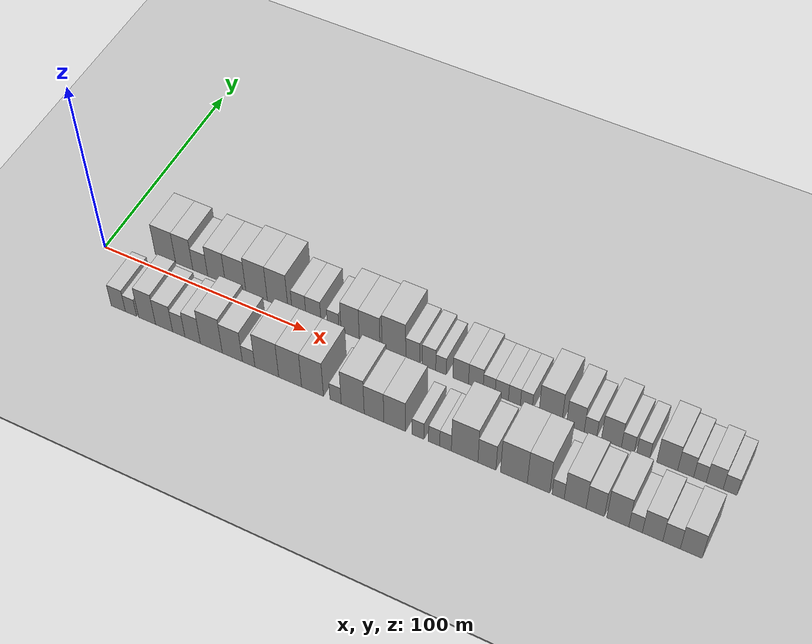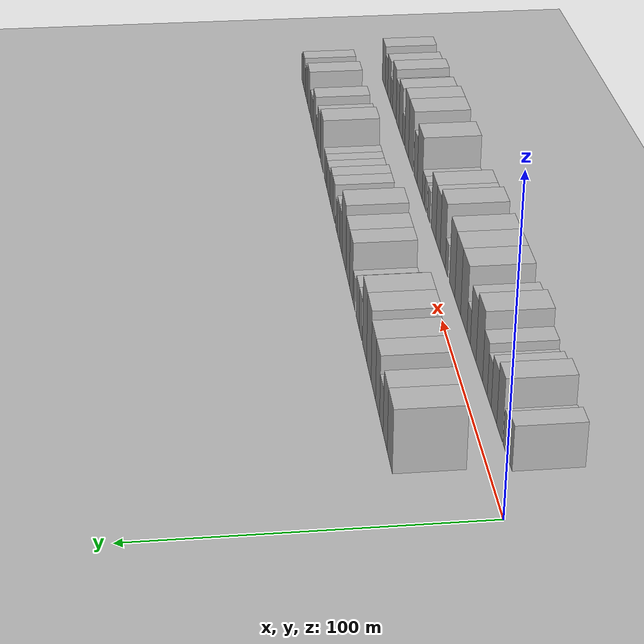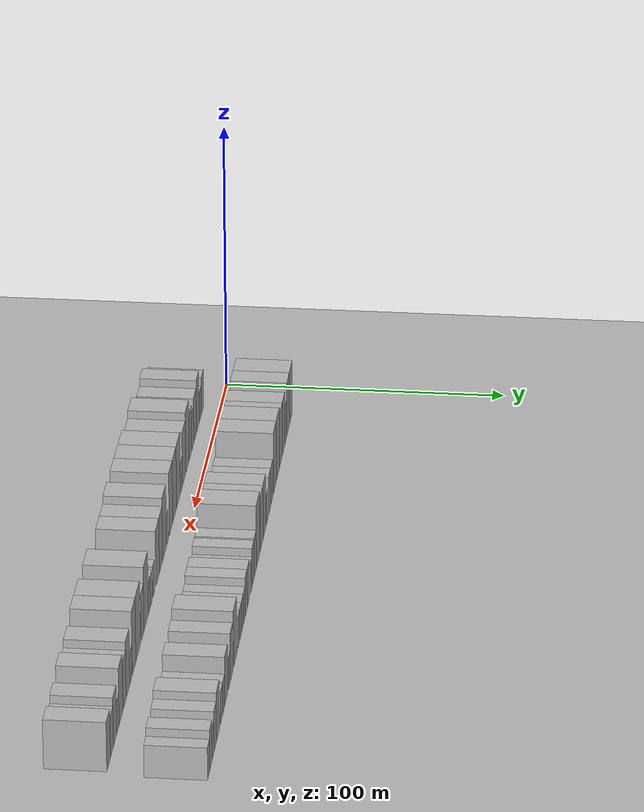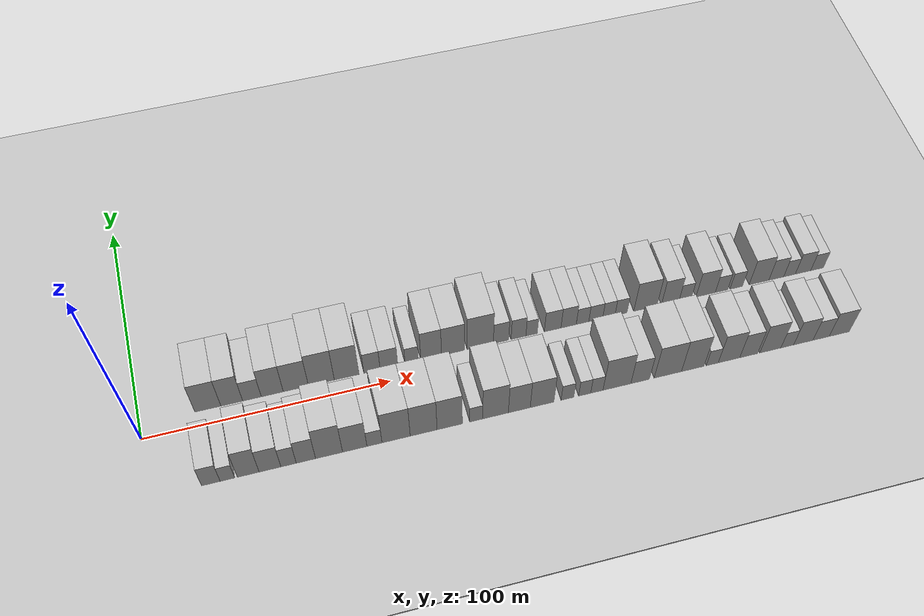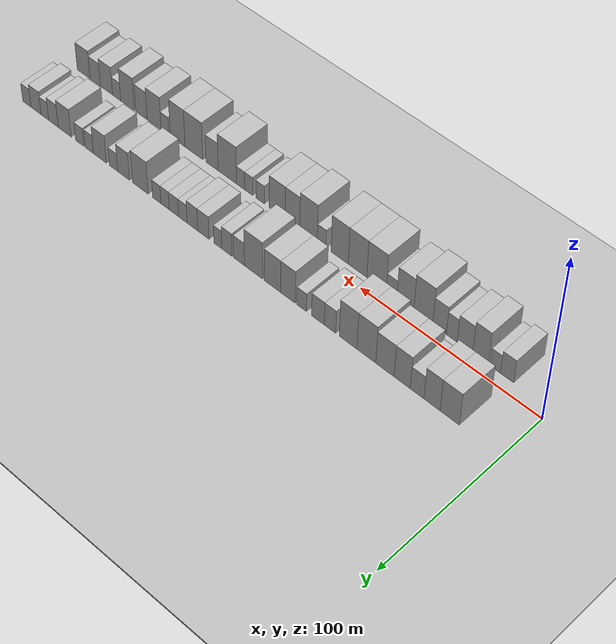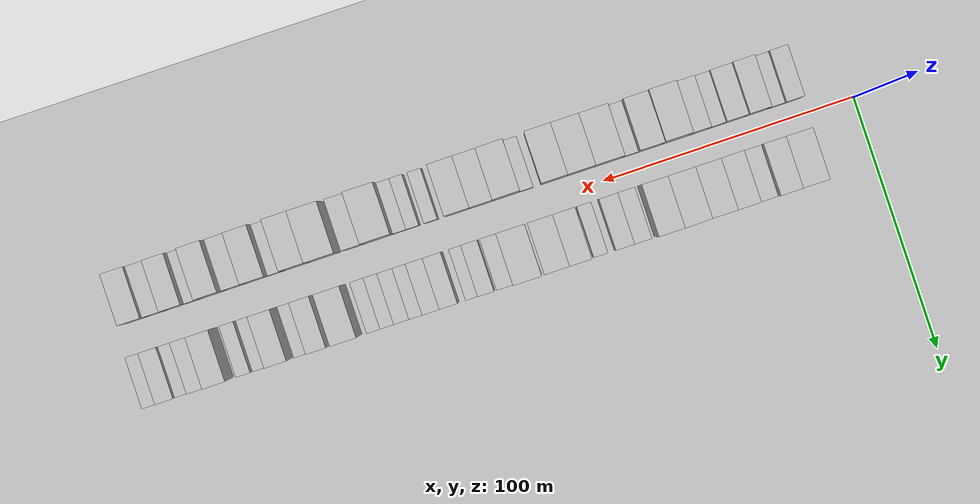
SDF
<?xml version="1.0" encoding="utf-8"?>

<sdf version="1.6">

   <world name="default">

      <gui fullscreen="0">

         <camera name="user_camera">

            <pose>-15 0 4.57585 0 0 0</pose>

            <view_controller>orbit</view_controller>

         </camera>

      </gui>

      <scene>

         <sky>

           <clouds>

             <speed>12</speed>

           </clouds>

         </sky>

         <ambient>0.4 0.4 0.4 1</ambient>

         <background>0.7 0.7 0.7 1</background>

         <shadows>1</shadows>

      </scene>

      <gravity>0 0 -9.8066</gravity>

      <magnetic_field>6e-06 2.3e-05 -4.2e-05</magnetic_field>

      <physics default="0" name="default_physics" type="ode">

         <ode>

            <solver>

               <type>quick</type>

               <iters>10</iters>

               <sor>1.0</sor>

               <use_dynamic_moi_rescaling>0</use_dynamic_moi_rescaling>

            </solver>

            <constraints>

               <cfm>0</cfm>

               <erp>0.2</erp>

               <contact_max_correcting_vel>100</contact_max_correcting_vel>

               <contact_surface_layer>0.001</contact_surface_layer>

            </constraints>

         </ode>

         <max_step_size>0.004</max_step_size>

         <real_time_factor>1</real_time_factor>

         <real_time_update_rate>250</real_time_update_rate>

      </physics>

      <light name="sun" type="directional">

         <cast_shadows>1</cast_shadows>

         <pose>0 0 10 0 0 0</pose>

         <diffuse>0.8 0.8 0.8 1</diffuse>

         <specular>0.2 0.2 0.2 1</specular>

         <attenuation>

            <range>1000</range>

            <constant>0.9</constant>

            <linear>0.01</linear>

            <quadratic>0.001</quadratic>

         </attenuation>

         <direction>-0.5 0.1 -0.9</direction>

      </light>

      <include>

         <name>ground_plane_1</name>

         <uri>model://HANNAS_ground_plane</uri>

         <pose>0 0 0  0 0 0</pose>

      </include>

      <include>

         <name>ground_plane_2</name>

         <uri>model://HANNAS_ground_plane</uri>

         <pose>100 0 0  0 0 0</pose>

      </include>

      <model name="building_1">

         <static>1</static>

         <pose frame="">27.1779 16.0000 0 0.000000 0.000000 1.570796</pose>

         <link name="link">

            <pose frame="">0 0 10.50 0 0 0</pose>

            <collision name="collision">

               <geometry>

                  <box>

                     <size>20.0000 10.3558 21.0000</size>

                  </box>

               </geometry>

               <max_contacts>10</max_contacts>

               <surface>

                  <contact>

                     <ode/>

                  </contact>

                  <bounce/>

                  <friction>

                     <torsional>

                        <ode/>

                     </torsional>

                     <ode/>

                  </friction>

               </surface>

            </collision>

            <visual name="visual">

               <cast_shadows>0</cast_shadows>

               <geometry>

                  <box>

                     <size>20.0000 10.3558 21.0000</size>

                  </box>

               </geometry>

               <material>

                  <script>

                     <uri>model://HANNAS_wall/materials/scripts</uri>

                     <uri>model://HANNAS_wall/materials/textures</uri>

                     <name>vrc/HANNAS_wall</name>

                  </script>

               </material>

            </visual>

            <self_collide>0</self_collide>

            <enable_wind>0</enable_wind>

            <kinematic>0</kinematic>

         </link>

      </model>

      <model name="building_2">

         <static>1</static>

         <pose frame="">36.7099 16.0000 0 0.000000 0.000000 1.570796</pose>

         <link name="link">

            <pose frame="">0 0 10.50 0 0 0</pose>

            <collision name="collision">

               <geometry>

                  <box>

                     <size>20.0000 8.7081 21.0000</size>

                  </box>

               </geometry>

               <max_contacts>10</max_contacts>

               <surface>

                  <contact>

                     <ode/>

                  </contact>

                  <bounce/>

                  <friction>

                     <torsional>

                        <ode/>

                     </torsional>

                     <ode/>

                  </friction>

               </surface>

            </collision>

            <visual name="visual">

               <cast_shadows>0</cast_shadows>

               <geometry>

                  <box>

                     <size>20.0000 8.7081 21.0000</size>

                  </box>

               </geometry>

               <material>

                  <script>

                     <uri>model://HANNAS_wall/materials/scripts</uri>

                     <uri>model://HANNAS_wall/materials/textures</uri>

                     <name>vrc/HANNAS_wall</name>

                  </script>

               </material>

            </visual>

            <self_collide>0</self_collide>

            <enable_wind>0</enable_wind>

            <kinematic>0</kinematic>

         </link>

      </model>

      <model name="building_3">

         <static>1</static>

         <pose frame="">44.7975 16.0000 0 0.000000 0.000000 1.570796</pose>

         <link name="link">

            <pose frame="">0 0 7.50 0 0 0</pose>

            <collision name="collision">

               <geometry>

                  <box>

                     <size>20.0000 7.4669 15.0000</size>

                  </box>

               </geometry>

               <max_contacts>10</max_contacts>

               <surface>

                  <contact>

                     <ode/>

                  </contact>

                  <bounce/>

                  <friction>

                     <torsional>

                        <ode/>

                     </torsional>

                     <ode/>

                  </friction>

               </surface>

            </collision>

            <visual name="visual">

               <cast_shadows>0</cast_shadows>

               <geometry>

                  <box>

                     <size>20.0000 7.4669 15.0000</size>

                  </box>

               </geometry>

               <material>

                  <script>

                     <uri>model://HANNAS_wall/materials/scripts</uri>

                     <uri>model://HANNAS_wall/materials/textures</uri>

                     <name>vrc/HANNAS_wall</name>

                  </script>

               </material>

            </visual>

            <self_collide>0</self_collide>

            <enable_wind>0</enable_wind>

            <kinematic>0</kinematic>

         </link>

      </model>

      <model name="building_4">

         <static>1</static>

         <pose frame="">52.9741 16.0000 0 0.000000 0.000000 1.570796</pose>

         <link name="link">

            <pose frame="">0 0 10.50 0 0 0</pose>

            <collision name="collision">

               <geometry>

                  <box>

                     <size>20.0000 8.8863 21.0000</size>

                  </box>

               </geometry>

               <max_contacts>10</max_contacts>

               <surface>

                  <contact>

                     <ode/>

                  </contact>

                  <bounce/>

                  <friction>

                     <torsional>

                        <ode/>

                     </torsional>

                     <ode/>

                  </friction>

               </surface>

            </collision>

            <visual name="visual">

               <cast_shadows>0</cast_shadows>

               <geometry>

                  <box>

                     <size>20.0000 8.8863 21.0000</size>

                  </box>

               </geometry>

               <material>

                  <script>

                     <uri>model://HANNAS_wall/materials/scripts</uri>

                     <uri>model://HANNAS_wall/materials/textures</uri>

                     <name>vrc/HANNAS_wall</name>

                  </script>

               </material>

            </visual>

            <self_collide>0</self_collide>

            <enable_wind>0</enable_wind>

            <kinematic>0</kinematic>

         </link>

      </model>

      <model name="building_5">

         <static>1</static>

         <pose frame="">62.5146 16.0000 0 0.000000 0.000000 1.570796</pose>

         <link name="link">

            <pose frame="">0 0 10.50 0 0 0</pose>

            <collision name="collision">

               <geometry>

                  <box>

                     <size>20.0000 10.1948 21.0000</size>

                  </box>

               </geometry>

               <max_contacts>10</max_contacts>

               <surface>

                  <contact>

                     <ode/>

                  </contact>

                  <bounce/>

                  <friction>

                     <torsional>

                        <ode/>

                     </torsional>

                     <ode/>

                  </friction>

               </surface>

            </collision>

            <visual name="visual">

               <cast_shadows>0</cast_shadows>

               <geometry>

                  <box>

                     <size>20.0000 10.1948 21.0000</size>

                  </box>

               </geometry>

               <material>

                  <script>

                     <uri>model://HANNAS_wall/materials/scripts</uri>

                     <uri>model://HANNAS_wall/materials/textures</uri>

                     <name>vrc/HANNAS_wall</name>

                  </script>

               </material>

            </visual>

            <self_collide>0</self_collide>

            <enable_wind>0</enable_wind>

            <kinematic>0</kinematic>

         </link>

      </model>

      <model name="building_6">

         <static>1</static>

         <pose frame="">72.9030 16.0000 0 0.000000 0.000000 1.570796</pose>

         <link name="link">

            <pose frame="">0 0 12.00 0 0 0</pose>

            <collision name="collision">

               <geometry>

                  <box>

                     <size>20.0000 10.5820 24.0000</size>

                  </box>

               </geometry>

               <max_contacts>10</max_contacts>

               <surface>

                  <contact>

                     <ode/>

                  </contact>

                  <bounce/>

                  <friction>

                     <torsional>

                        <ode/>

                     </torsional>

                     <ode/>

                  </friction>

               </surface>

            </collision>

            <visual name="visual">

               <cast_shadows>0</cast_shadows>

               <geometry>

                  <box>

                     <size>20.0000 10.5820 24.0000</size>

                  </box>

               </geometry>

               <material>

                  <script>

                     <uri>model://HANNAS_wall/materials/scripts</uri>

                     <uri>model://HANNAS_wall/materials/textures</uri>

                     <name>vrc/HANNAS_wall</name>

                  </script>

               </material>

            </visual>

            <self_collide>0</self_collide>

            <enable_wind>0</enable_wind>

            <kinematic>0</kinematic>

         </link>

      </model>

      <model name="building_7">

         <static>1</static>

         <pose frame="">83.2527 16.0000 0 0.000000 0.000000 1.570796</pose>

         <link name="link">

            <pose frame="">0 0 12.00 0 0 0</pose>

            <collision name="collision">

               <geometry>

                  <box>

                     <size>20.0000 10.1174 24.0000</size>

                  </box>

               </geometry>

               <max_contacts>10</max_contacts>

               <surface>

                  <contact>

                     <ode/>

                  </contact>

                  <bounce/>

                  <friction>

                     <torsional>

                        <ode/>

                     </torsional>

                     <ode/>

                  </friction>

               </surface>

            </collision>

            <visual name="visual">

               <cast_shadows>0</cast_shadows>

               <geometry>

                  <box>

                     <size>20.0000 10.1174 24.0000</size>

                  </box>

               </geometry>

               <material>

                  <script>

                     <uri>model://HANNAS_wall/materials/scripts</uri>

                     <uri>model://HANNAS_wall/materials/textures</uri>

                     <name>vrc/HANNAS_wall</name>

                  </script>

               </material>

            </visual>

            <self_collide>0</self_collide>

            <enable_wind>0</enable_wind>

            <kinematic>0</kinematic>

         </link>

      </model>

      <model name="building_8">

         <static>1</static>

         <pose frame="">93.6580 16.0000 0 0.000000 0.000000 1.570796</pose>

         <link name="link">

            <pose frame="">0 0 7.50 0 0 0</pose>

            <collision name="collision">

               <geometry>

                  <box>

                     <size>20.0000 6.6933 15.0000</size>

                  </box>

               </geometry>

               <max_contacts>10</max_contacts>

               <surface>

                  <contact>

                     <ode/>

                  </contact>

                  <bounce/>

                  <friction>

                     <torsional>

                        <ode/>

                     </torsional>

                     <ode/>

                  </friction>

               </surface>

            </collision>

            <visual name="visual">

               <cast_shadows>0</cast_shadows>

               <geometry>

                  <box>

                     <size>20.0000 6.6933 15.0000</size>

                  </box>

               </geometry>

               <material>

                  <script>

                     <uri>model://HANNAS_wall/materials/scripts</uri>

                     <uri>model://HANNAS_wall/materials/textures</uri>

                     <name>vrc/HANNAS_wall</name>

                  </script>

               </material>

            </visual>

            <self_collide>0</self_collide>

            <enable_wind>0</enable_wind>

            <kinematic>0</kinematic>

         </link>

      </model>

      <model name="building_9">

         <static>1</static>

         <pose frame="">100.6580 16.0000 0 0.000000 0.000000 1.570796</pose>

         <link name="link">

            <pose frame="">0 0 7.50 0 0 0</pose>

            <collision name="collision">

               <geometry>

                  <box>

                     <size>20.0000 7.3065 15.0000</size>

                  </box>

               </geometry>

               <max_contacts>10</max_contacts>

               <surface>

                  <contact>

                     <ode/>

                  </contact>

                  <bounce/>

                  <friction>

                     <torsional>

                        <ode/>

                     </torsional>

                     <ode/>

                  </friction>

               </surface>

            </collision>

            <visual name="visual">

               <cast_shadows>0</cast_shadows>

               <geometry>

                  <box>

                     <size>20.0000 7.3065 15.0000</size>

                  </box>

               </geometry>

               <material>

                  <script>

                     <uri>model://HANNAS_wall/materials/scripts</uri>

                     <uri>model://HANNAS_wall/materials/textures</uri>

                     <name>vrc/HANNAS_wall</name>

                  </script>

               </material>

            </visual>

            <self_collide>0</self_collide>

            <enable_wind>0</enable_wind>

            <kinematic>0</kinematic>

         </link>

      </model>

      <model name="building_10">

         <static>1</static>

         <pose frame="">110.0978 16.0000 0 0.000000 0.000000 1.570796</pose>

         <link name="link">

            <pose frame="">0 0 6.00 0 0 0</pose>

            <collision name="collision">

               <geometry>

                  <box>

                     <size>20.0000 5.5731 12.0000</size>

                  </box>

               </geometry>

               <max_contacts>10</max_contacts>

               <surface>

                  <contact>

                     <ode/>

                  </contact>

                  <bounce/>

                  <friction>

                     <torsional>

                        <ode/>

                     </torsional>

                     <ode/>

                  </friction>

               </surface>

            </collision>

            <visual name="visual">

               <cast_shadows>0</cast_shadows>

               <geometry>

                  <box>

                     <size>20.0000 5.5731 12.0000</size>

                  </box>

               </geometry>

               <material>

                  <script>

                     <uri>model://HANNAS_wall/materials/scripts</uri>

                     <uri>model://HANNAS_wall/materials/textures</uri>

                     <name>vrc/HANNAS_wall</name>

                  </script>

               </material>

            </visual>

            <self_collide>0</self_collide>

            <enable_wind>0</enable_wind>

            <kinematic>0</kinematic>

         </link>

      </model>

      <model name="building_11">

         <static>1</static>

         <pose frame="">118.2044 16.0000 0 0.000000 0.000000 1.570796</pose>

         <link name="link">

            <pose frame="">0 0 10.50 0 0 0</pose>

            <collision name="collision">

               <geometry>

                  <box>

                     <size>20.0000 8.6402 21.0000</size>

                  </box>

               </geometry>

               <max_contacts>10</max_contacts>

               <surface>

                  <contact>

                     <ode/>

                  </contact>

                  <bounce/>

                  <friction>

                     <torsional>

                        <ode/>

                     </torsional>

                     <ode/>

                  </friction>

               </surface>

            </collision>

            <visual name="visual">

               <cast_shadows>0</cast_shadows>

               <geometry>

                  <box>

                     <size>20.0000 8.6402 21.0000</size>

                  </box>

               </geometry>

               <material>

                  <script>

                     <uri>model://HANNAS_wall/materials/scripts</uri>

                     <uri>model://HANNAS_wall/materials/textures</uri>

                     <name>vrc/HANNAS_wall</name>

                  </script>

               </material>

            </visual>

            <self_collide>0</self_collide>

            <enable_wind>0</enable_wind>

            <kinematic>0</kinematic>

         </link>

      </model>

      <model name="building_12">

         <static>1</static>

         <pose frame="">127.4132 16.0000 0 0.000000 0.000000 1.570796</pose>

         <link name="link">

            <pose frame="">0 0 10.50 0 0 0</pose>

            <collision name="collision">

               <geometry>

                  <box>

                     <size>20.0000 9.7773 21.0000</size>

                  </box>

               </geometry>

               <max_contacts>10</max_contacts>

               <surface>

                  <contact>

                     <ode/>

                  </contact>

                  <bounce/>

                  <friction>

                     <torsional>

                        <ode/>

                     </torsional>

                     <ode/>

                  </friction>

               </surface>

            </collision>

            <visual name="visual">

               <cast_shadows>0</cast_shadows>

               <geometry>

                  <box>

                     <size>20.0000 9.7773 21.0000</size>

                  </box>

               </geometry>

               <material>

                  <script>

                     <uri>model://HANNAS_wall/materials/scripts</uri>

                     <uri>model://HANNAS_wall/materials/textures</uri>

                     <name>vrc/HANNAS_wall</name>

                  </script>

               </material>

            </visual>

            <self_collide>0</self_collide>

            <enable_wind>0</enable_wind>

            <kinematic>0</kinematic>

         </link>

      </model>

      <model name="building_13">

         <static>1</static>

         <pose frame="">138.8312 16.0000 0 0.000000 0.000000 1.570796</pose>

         <link name="link">

            <pose frame="">0 0 12.00 0 0 0</pose>

            <collision name="collision">

               <geometry>

                  <box>

                     <size>20.0000 11.0585 24.0000</size>

                  </box>

               </geometry>

               <max_contacts>10</max_contacts>

               <surface>

                  <contact>

                     <ode/>

                  </contact>

                  <bounce/>

                  <friction>

                     <torsional>

                        <ode/>

                     </torsional>

                     <ode/>

                  </friction>

               </surface>

            </collision>

            <visual name="visual">

               <cast_shadows>0</cast_shadows>

               <geometry>

                  <box>

                     <size>20.0000 11.0585 24.0000</size>

                  </box>

               </geometry>

               <material>

                  <script>

                     <uri>model://HANNAS_wall/materials/scripts</uri>

                     <uri>model://HANNAS_wall/materials/textures</uri>

                     <name>vrc/HANNAS_wall</name>

                  </script>

               </material>

            </visual>

            <self_collide>0</self_collide>

            <enable_wind>0</enable_wind>

            <kinematic>0</kinematic>

         </link>

      </model>

      <model name="building_14">

         <static>1</static>

         <pose frame="">147.6243 16.0000 0 0.000000 0.000000 1.570796</pose>

         <link name="link">

            <pose frame="">0 0 7.50 0 0 0</pose>

            <collision name="collision">

               <geometry>

                  <box>

                     <size>20.0000 6.5277 15.0000</size>

                  </box>

               </geometry>

               <max_contacts>10</max_contacts>

               <surface>

                  <contact>

                     <ode/>

                  </contact>

                  <bounce/>

                  <friction>

                     <torsional>

                        <ode/>

                     </torsional>

                     <ode/>

                  </friction>

               </surface>

            </collision>

            <visual name="visual">

               <cast_shadows>0</cast_shadows>

               <geometry>

                  <box>

                     <size>20.0000 6.5277 15.0000</size>

                  </box>

               </geometry>

               <material>

                  <script>

                     <uri>model://HANNAS_wall/materials/scripts</uri>

                     <uri>model://HANNAS_wall/materials/textures</uri>

                     <name>vrc/HANNAS_wall</name>

                  </script>

               </material>

            </visual>

            <self_collide>0</self_collide>

            <enable_wind>0</enable_wind>

            <kinematic>0</kinematic>

         </link>

      </model>

      <model name="building_15">

         <static>1</static>

         <pose frame="">155.0509 16.0000 0 0.000000 0.000000 1.570796</pose>

         <link name="link">

            <pose frame="">0 0 7.50 0 0 0</pose>

            <collision name="collision">

               <geometry>

                  <box>

                     <size>20.0000 6.3255 15.0000</size>

                  </box>

               </geometry>

               <max_contacts>10</max_contacts>

               <surface>

                  <contact>

                     <ode/>

                  </contact>

                  <bounce/>

                  <friction>

                     <torsional>

                        <ode/>

                     </torsional>

                     <ode/>

                  </friction>

               </surface>

            </collision>

            <visual name="visual">

               <cast_shadows>0</cast_shadows>

               <geometry>

                  <box>

                     <size>20.0000 6.3255 15.0000</size>

                  </box>

               </geometry>

               <material>

                  <script>

                     <uri>model://HANNAS_wall/materials/scripts</uri>

                     <uri>model://HANNAS_wall/materials/textures</uri>

                     <name>vrc/HANNAS_wall</name>

                  </script>

               </material>

            </visual>

            <self_collide>0</self_collide>

            <enable_wind>0</enable_wind>

            <kinematic>0</kinematic>

         </link>

      </model>

      <model name="building_16">

         <static>1</static>

         <pose frame="">160.6476 16.0000 0 0.000000 0.000000 1.570796</pose>

         <link name="link">

            <pose frame="">0 0 6.00 0 0 0</pose>

            <collision name="collision">

               <geometry>

                  <box>

                     <size>20.0000 4.8679 12.0000</size>

                  </box>

               </geometry>

               <max_contacts>10</max_contacts>

               <surface>

                  <contact>

                     <ode/>

                  </contact>

                  <bounce/>

                  <friction>

                     <torsional>

                        <ode/>

                     </torsional>

                     <ode/>

                  </friction>

               </surface>

            </collision>

            <visual name="visual">

               <cast_shadows>0</cast_shadows>

               <geometry>

                  <box>

                     <size>20.0000 4.8679 12.0000</size>

                  </box>

               </geometry>

               <material>

                  <script>

                     <uri>model://HANNAS_wall/materials/scripts</uri>

                     <uri>model://HANNAS_wall/materials/textures</uri>

                     <name>vrc/HANNAS_wall</name>

                  </script>

               </material>

            </visual>

            <self_collide>0</self_collide>

            <enable_wind>0</enable_wind>

            <kinematic>0</kinematic>

         </link>

      </model>

      <model name="building_17">

         <static>1</static>

         <pose frame="">169.6573 16.0000 0 0.000000 0.000000 1.570796</pose>

         <link name="link">

            <pose frame="">0 0 7.50 0 0 0</pose>

            <collision name="collision">

               <geometry>

                  <box>

                     <size>20.0000 7.1515 15.0000</size>

                  </box>

               </geometry>

               <max_contacts>10</max_contacts>

               <surface>

                  <contact>

                     <ode/>

                  </contact>

                  <bounce/>

                  <friction>

                     <torsional>

                        <ode/>

                     </torsional>

                     <ode/>

                  </friction>

               </surface>

            </collision>

            <visual name="visual">

               <cast_shadows>0</cast_shadows>

               <geometry>

                  <box>

                     <size>20.0000 7.1515 15.0000</size>

                  </box>

               </geometry>

               <material>

                  <script>

                     <uri>model://HANNAS_wall/materials/scripts</uri>

                     <uri>model://HANNAS_wall/materials/textures</uri>

                     <name>vrc/HANNAS_wall</name>

                  </script>

               </material>

            </visual>

            <self_collide>0</self_collide>

            <enable_wind>0</enable_wind>

            <kinematic>0</kinematic>

         </link>

      </model>

      <model name="building_18">

         <static>1</static>

         <pose frame="">176.5369 16.0000 0 0.000000 0.000000 1.570796</pose>

         <link name="link">

            <pose frame="">0 0 7.50 0 0 0</pose>

            <collision name="collision">

               <geometry>

                  <box>

                     <size>20.0000 6.6078 15.0000</size>

                  </box>

               </geometry>

               <max_contacts>10</max_contacts>

               <surface>

                  <contact>

                     <ode/>

                  </contact>

                  <bounce/>

                  <friction>

                     <torsional>

                        <ode/>

                     </torsional>

                     <ode/>

                  </friction>

               </surface>

            </collision>

            <visual name="visual">

               <cast_shadows>0</cast_shadows>

               <geometry>

                  <box>

                     <size>20.0000 6.6078 15.0000</size>

                  </box>

               </geometry>

               <material>

                  <script>

                     <uri>model://HANNAS_wall/materials/scripts</uri>

                     <uri>model://HANNAS_wall/materials/textures</uri>

                     <name>vrc/HANNAS_wall</name>

                  </script>

               </material>

            </visual>

            <self_collide>0</self_collide>

            <enable_wind>0</enable_wind>

            <kinematic>0</kinematic>

         </link>

      </model>

      <model name="building_19">

         <static>1</static>

         <pose frame="">182.5508 16.0000 0 0.000000 0.000000 1.570796</pose>

         <link name="link">

            <pose frame="">0 0 6.00 0 0 0</pose>

            <collision name="collision">

               <geometry>

                  <box>

                     <size>20.0000 5.4199 12.0000</size>

                  </box>

               </geometry>

               <max_contacts>10</max_contacts>

               <surface>

                  <contact>

                     <ode/>

                  </contact>

                  <bounce/>

                  <friction>

                     <torsional>

                        <ode/>

                     </torsional>

                     <ode/>

                  </friction>

               </surface>

            </collision>

            <visual name="visual">

               <cast_shadows>0</cast_shadows>

               <geometry>

                  <box>

                     <size>20.0000 5.4199 12.0000</size>

                  </box>

               </geometry>

               <material>

                  <script>

                     <uri>model://HANNAS_wall/materials/scripts</uri>

                     <uri>model://HANNAS_wall/materials/textures</uri>

                     <name>vrc/HANNAS_wall</name>

                  </script>

               </material>

            </visual>

            <self_collide>0</self_collide>

            <enable_wind>0</enable_wind>

            <kinematic>0</kinematic>

         </link>

      </model>

      <model name="building_20">

         <static>1</static>

         <pose frame="">188.2551 16.0000 0 0.000000 0.000000 1.570796</pose>

         <link name="link">

            <pose frame="">0 0 6.00 0 0 0</pose>

            <collision name="collision">

               <geometry>

                  <box>

                     <size>20.0000 5.9887 12.0000</size>

                  </box>

               </geometry>

               <max_contacts>10</max_contacts>

               <surface>

                  <contact>

                     <ode/>

                  </contact>

                  <bounce/>

                  <friction>

                     <torsional>

                        <ode/>

                     </torsional>

                     <ode/>

                  </friction>

               </surface>

            </collision>

            <visual name="visual">

               <cast_shadows>0</cast_shadows>

               <geometry>

                  <box>

                     <size>20.0000 5.9887 12.0000</size>

                  </box>

               </geometry>

               <material>

                  <script>

                     <uri>model://HANNAS_wall/materials/scripts</uri>

                     <uri>model://HANNAS_wall/materials/textures</uri>

                     <name>vrc/HANNAS_wall</name>

                  </script>

               </material>

            </visual>

            <self_collide>0</self_collide>

            <enable_wind>0</enable_wind>

            <kinematic>0</kinematic>

         </link>

      </model>

      <model name="building_21">

         <static>1</static>

         <pose frame="">193.9157 16.0000 0 0.000000 0.000000 1.570796</pose>

         <link name="link">

            <pose frame="">0 0 6.00 0 0 0</pose>

            <collision name="collision">

               <geometry>

                  <box>

                     <size>20.0000 5.3326 12.0000</size>

                  </box>

               </geometry>

               <max_contacts>10</max_contacts>

               <surface>

                  <contact>

                     <ode/>

                  </contact>

                  <bounce/>

                  <friction>

                     <torsional>

                        <ode/>

                     </torsional>

                     <ode/>

                  </friction>

               </surface>

            </collision>

            <visual name="visual">

               <cast_shadows>0</cast_shadows>

               <geometry>

                  <box>

                     <size>20.0000 5.3326 12.0000</size>

                  </box>

               </geometry>

               <material>

                  <script>

                     <uri>model://HANNAS_wall/materials/scripts</uri>

                     <uri>model://HANNAS_wall/materials/textures</uri>

                     <name>vrc/HANNAS_wall</name>

                  </script>

               </material>

            </visual>

            <self_collide>0</self_collide>

            <enable_wind>0</enable_wind>

            <kinematic>0</kinematic>

         </link>

      </model>

      <model name="building_22">

         <static>1</static>

         <pose frame="">199.2230 16.0000 0 0.000000 0.000000 1.570796</pose>

         <link name="link">

            <pose frame="">0 0 6.00 0 0 0</pose>

            <collision name="collision">

               <geometry>

                  <box>

                     <size>20.0000 5.2819 12.0000</size>

                  </box>

               </geometry>

               <max_contacts>10</max_contacts>

               <surface>

                  <contact>

                     <ode/>

                  </contact>

                  <bounce/>

                  <friction>

                     <torsional>

                        <ode/>

                     </torsional>

                     <ode/>

                  </friction>

               </surface>

            </collision>

            <visual name="visual">

               <cast_shadows>0</cast_shadows>

               <geometry>

                  <box>

                     <size>20.0000 5.2819 12.0000</size>

                  </box>

               </geometry>

               <material>

                  <script>

                     <uri>model://HANNAS_wall/materials/scripts</uri>

                     <uri>model://HANNAS_wall/materials/textures</uri>

                     <name>vrc/HANNAS_wall</name>

                  </script>

               </material>

            </visual>

            <self_collide>0</self_collide>

            <enable_wind>0</enable_wind>

            <kinematic>0</kinematic>

         </link>

      </model>

      <model name="building_23">

         <static>1</static>

         <pose frame="">209.9373 16.0000 0 0.000000 0.000000 1.570796</pose>

         <link name="link">

            <pose frame="">0 0 10.50 0 0 0</pose>

            <collision name="collision">

               <geometry>

                  <box>

                     <size>20.0000 10.1466 21.0000</size>

                  </box>

               </geometry>

               <max_contacts>10</max_contacts>

               <surface>

                  <contact>

                     <ode/>

                  </contact>

                  <bounce/>

                  <friction>

                     <torsional>

                        <ode/>

                     </torsional>

                     <ode/>

                  </friction>

               </surface>

            </collision>

            <visual name="visual">

               <cast_shadows>0</cast_shadows>

               <geometry>

                  <box>

                     <size>20.0000 10.1466 21.0000</size>

                  </box>

               </geometry>

               <material>

                  <script>

                     <uri>model://HANNAS_wall/materials/scripts</uri>

                     <uri>model://HANNAS_wall/materials/textures</uri>

                     <name>vrc/HANNAS_wall</name>

                  </script>

               </material>

            </visual>

            <self_collide>0</self_collide>

            <enable_wind>0</enable_wind>

            <kinematic>0</kinematic>

         </link>

      </model>

      <model name="building_24">

         <static>1</static>

         <pose frame="">220.8997 16.0000 0 0.000000 0.000000 1.570796</pose>

         <link name="link">

            <pose frame="">0 0 9.00 0 0 0</pose>

            <collision name="collision">

               <geometry>

                  <box>

                     <size>20.0000 7.7781 18.0000</size>

                  </box>

               </geometry>

               <max_contacts>10</max_contacts>

               <surface>

                  <contact>

                     <ode/>

                  </contact>

                  <bounce/>

                  <friction>

                     <torsional>

                        <ode/>

                     </torsional>

                     <ode/>

                  </friction>

               </surface>

            </collision>

            <visual name="visual">

               <cast_shadows>0</cast_shadows>

               <geometry>

                  <box>

                     <size>20.0000 7.7781 18.0000</size>

                  </box>

               </geometry>

               <material>

                  <script>

                     <uri>model://HANNAS_wall/materials/scripts</uri>

                     <uri>model://HANNAS_wall/materials/textures</uri>

                     <name>vrc/HANNAS_wall</name>

                  </script>

               </material>

            </visual>

            <self_collide>0</self_collide>

            <enable_wind>0</enable_wind>

            <kinematic>0</kinematic>

         </link>

      </model>

      <model name="building_25">

         <static>1</static>

         <pose frame="">227.5422 16.0000 0 0.000000 0.000000 1.570796</pose>

         <link name="link">

            <pose frame="">0 0 6.00 0 0 0</pose>

            <collision name="collision">

               <geometry>

                  <box>

                     <size>20.0000 5.5069 12.0000</size>

                  </box>

               </geometry>

               <max_contacts>10</max_contacts>

               <surface>

                  <contact>

                     <ode/>

                  </contact>

                  <bounce/>

                  <friction>

                     <torsional>

                        <ode/>

                     </torsional>

                     <ode/>

                  </friction>

               </surface>

            </collision>

            <visual name="visual">

               <cast_shadows>0</cast_shadows>

               <geometry>

                  <box>

                     <size>20.0000 5.5069 12.0000</size>

                  </box>

               </geometry>

               <material>

                  <script>

                     <uri>model://HANNAS_wall/materials/scripts</uri>

                     <uri>model://HANNAS_wall/materials/textures</uri>

                     <name>vrc/HANNAS_wall</name>

                  </script>

               </material>

            </visual>

            <self_collide>0</self_collide>

            <enable_wind>0</enable_wind>

            <kinematic>0</kinematic>

         </link>

      </model>

      <model name="building_26">

         <static>1</static>

         <pose frame="">236.6096 16.0000 0 0.000000 0.000000 1.570796</pose>

         <link name="link">

            <pose frame="">0 0 9.00 0 0 0</pose>

            <collision name="collision">

               <geometry>

                  <box>

                     <size>20.0000 8.6280 18.0000</size>

                  </box>

               </geometry>

               <max_contacts>10</max_contacts>

               <surface>

                  <contact>

                     <ode/>

                  </contact>

                  <bounce/>

                  <friction>

                     <torsional>

                        <ode/>

                     </torsional>

                     <ode/>

                  </friction>

               </surface>

            </collision>

            <visual name="visual">

               <cast_shadows>0</cast_shadows>

               <geometry>

                  <box>

                     <size>20.0000 8.6280 18.0000</size>

                  </box>

               </geometry>

               <material>

                  <script>

                     <uri>model://HANNAS_wall/materials/scripts</uri>

                     <uri>model://HANNAS_wall/materials/textures</uri>

                     <name>vrc/HANNAS_wall</name>

                  </script>

               </material>

            </visual>

            <self_collide>0</self_collide>

            <enable_wind>0</enable_wind>

            <kinematic>0</kinematic>

         </link>

      </model>

      <model name="building_27">

         <static>1</static>

         <pose frame="">243.6946 16.0000 0 0.000000 0.000000 1.570796</pose>

         <link name="link">

            <pose frame="">0 0 6.00 0 0 0</pose>

            <collision name="collision">

               <geometry>

                  <box>

                     <size>20.0000 5.5418 12.0000</size>

                  </box>

               </geometry>

               <max_contacts>10</max_contacts>

               <surface>

                  <contact>

                     <ode/>

                  </contact>

                  <bounce/>

                  <friction>

                     <torsional>

                        <ode/>

                     </torsional>

                     <ode/>

                  </friction>

               </surface>

            </collision>

            <visual name="visual">

               <cast_shadows>0</cast_shadows>

               <geometry>

                  <box>

                     <size>20.0000 5.5418 12.0000</size>

                  </box>

               </geometry>

               <material>

                  <script>

                     <uri>model://HANNAS_wall/materials/scripts</uri>

                     <uri>model://HANNAS_wall/materials/textures</uri>

                     <name>vrc/HANNAS_wall</name>

                  </script>

               </material>

            </visual>

            <self_collide>0</self_collide>

            <enable_wind>0</enable_wind>

            <kinematic>0</kinematic>

         </link>

      </model>

      <model name="building_28">

         <static>1</static>

         <pose frame="">250.2726 16.0000 0 0.000000 0.000000 1.570796</pose>

         <link name="link">

            <pose frame="">0 0 6.00 0 0 0</pose>

            <collision name="collision">

               <geometry>

                  <box>

                     <size>20.0000 5.6143 12.0000</size>

                  </box>

               </geometry>

               <max_contacts>10</max_contacts>

               <surface>

                  <contact>

                     <ode/>

                  </contact>

                  <bounce/>

                  <friction>

                     <torsional>

                        <ode/>

                     </torsional>

                     <ode/>

                  </friction>

               </surface>

            </collision>

            <visual name="visual">

               <cast_shadows>0</cast_shadows>

               <geometry>

                  <box>

                     <size>20.0000 5.6143 12.0000</size>

                  </box>

               </geometry>

               <material>

                  <script>

                     <uri>model://HANNAS_wall/materials/scripts</uri>

                     <uri>model://HANNAS_wall/materials/textures</uri>

                     <name>vrc/HANNAS_wall</name>

                  </script>

               </material>

            </visual>

            <self_collide>0</self_collide>

            <enable_wind>0</enable_wind>

            <kinematic>0</kinematic>

         </link>

      </model>

      <model name="building_29">

         <static>1</static>

         <pose frame="">260.5104 16.0000 0 0.000000 0.000000 1.570796</pose>

         <link name="link">

            <pose frame="">0 0 9.00 0 0 0</pose>

            <collision name="collision">

               <geometry>

                  <box>

                     <size>20.0000 8.8612 18.0000</size>

                  </box>

               </geometry>

               <max_contacts>10</max_contacts>

               <surface>

                  <contact>

                     <ode/>

                  </contact>

                  <bounce/>

                  <friction>

                     <torsional>

                        <ode/>

                     </torsional>

                     <ode/>

                  </friction>

               </surface>

            </collision>

            <visual name="visual">

               <cast_shadows>0</cast_shadows>

               <geometry>

                  <box>

                     <size>20.0000 8.8612 18.0000</size>

                  </box>

               </geometry>

               <material>

                  <script>

                     <uri>model://HANNAS_wall/materials/scripts</uri>

                     <uri>model://HANNAS_wall/materials/textures</uri>

                     <name>vrc/HANNAS_wall</name>

                  </script>

               </material>

            </visual>

            <self_collide>0</self_collide>

            <enable_wind>0</enable_wind>

            <kinematic>0</kinematic>

         </link>

      </model>

      <model name="building_30">

         <static>1</static>

         <pose frame="">268.3135 16.0000 0 0.000000 0.000000 1.570796</pose>

         <link name="link">

            <pose frame="">0 0 7.50 0 0 0</pose>

            <collision name="collision">

               <geometry>

                  <box>

                     <size>20.0000 6.7450 15.0000</size>

                  </box>

               </geometry>

               <max_contacts>10</max_contacts>

               <surface>

                  <contact>

                     <ode/>

                  </contact>

                  <bounce/>

                  <friction>

                     <torsional>

                        <ode/>

                     </torsional>

                     <ode/>

                  </friction>

               </surface>

            </collision>

            <visual name="visual">

               <cast_shadows>0</cast_shadows>

               <geometry>

                  <box>

                     <size>20.0000 6.7450 15.0000</size>

                  </box>

               </geometry>

               <material>

                  <script>

                     <uri>model://HANNAS_wall/materials/scripts</uri>

                     <uri>model://HANNAS_wall/materials/textures</uri>

                     <name>vrc/HANNAS_wall</name>

                  </script>

               </material>

            </visual>

            <self_collide>0</self_collide>

            <enable_wind>0</enable_wind>

            <kinematic>0</kinematic>

         </link>

      </model>

      <model name="building_31">

         <static>1</static>

         <pose frame="">274.3185 16.0000 0 0.000000 0.000000 1.570796</pose>

         <link name="link">

            <pose frame="">0 0 6.00 0 0 0</pose>

            <collision name="collision">

               <geometry>

                  <box>

                     <size>20.0000 5.2650 12.0000</size>

                  </box>

               </geometry>

               <max_contacts>10</max_contacts>

               <surface>

                  <contact>

                     <ode/>

                  </contact>

                  <bounce/>

                  <friction>

                     <torsional>

                        <ode/>

                     </torsional>

                     <ode/>

                  </friction>

               </surface>

            </collision>

            <visual name="visual">

               <cast_shadows>0</cast_shadows>

               <geometry>

                  <box>

                     <size>20.0000 5.2650 12.0000</size>

                  </box>

               </geometry>

               <material>

                  <script>

                     <uri>model://HANNAS_wall/materials/scripts</uri>

                     <uri>model://HANNAS_wall/materials/textures</uri>

                     <name>vrc/HANNAS_wall</name>

                  </script>

               </material>

            </visual>

            <self_collide>0</self_collide>

            <enable_wind>0</enable_wind>

            <kinematic>0</kinematic>

         </link>

      </model>

      <model name="building_32">

         <static>1</static>

         <pose frame="">280.4677 16.0000 0 0.000000 0.000000 1.570796</pose>

         <link name="link">

            <pose frame="">0 0 7.50 0 0 0</pose>

            <collision name="collision">

               <geometry>

                  <box>

                     <size>20.0000 7.0334 15.0000</size>

                  </box>

               </geometry>

               <max_contacts>10</max_contacts>

               <surface>

                  <contact>

                     <ode/>

                  </contact>

                  <bounce/>

                  <friction>

                     <torsional>

                        <ode/>

                     </torsional>

                     <ode/>

                  </friction>

               </surface>

            </collision>

            <visual name="visual">

               <cast_shadows>0</cast_shadows>

               <geometry>

                  <box>

                     <size>20.0000 7.0334 15.0000</size>

                  </box>

               </geometry>

               <material>

                  <script>

                     <uri>model://HANNAS_wall/materials/scripts</uri>

                     <uri>model://HANNAS_wall/materials/textures</uri>

                     <name>vrc/HANNAS_wall</name>

                  </script>

               </material>

            </visual>

            <self_collide>0</self_collide>

            <enable_wind>0</enable_wind>

            <kinematic>0</kinematic>

         </link>

      </model>

      <model name="building_33">

         <static>1</static>

         <pose frame="">286.8735 16.0000 0 0.000000 0.000000 1.570796</pose>

         <link name="link">

            <pose frame="">0 0 6.00 0 0 0</pose>

            <collision name="collision">

               <geometry>

                  <box>

                     <size>20.0000 5.7783 12.0000</size>

                  </box>

               </geometry>

               <max_contacts>10</max_contacts>

               <surface>

                  <contact>

                     <ode/>

                  </contact>

                  <bounce/>

                  <friction>

                     <torsional>

                        <ode/>

                     </torsional>

                     <ode/>

                  </friction>

               </surface>

            </collision>

            <visual name="visual">

               <cast_shadows>0</cast_shadows>

               <geometry>

                  <box>

                     <size>20.0000 5.7783 12.0000</size>

                  </box>

               </geometry>

               <material>

                  <script>

                     <uri>model://HANNAS_wall/materials/scripts</uri>

                     <uri>model://HANNAS_wall/materials/textures</uri>

                     <name>vrc/HANNAS_wall</name>

                  </script>

               </material>

            </visual>

            <self_collide>0</self_collide>

            <enable_wind>0</enable_wind>

            <kinematic>0</kinematic>

         </link>

      </model>

      <model name="building_34">

         <static>1</static>

         <pose frame="">23.5698 -16.0000 0 0.000000 0.000000 1.570796</pose>

         <link name="link">

            <pose frame="">0 0 7.50 0 0 0</pose>

            <collision name="collision">

               <geometry>

                  <box>

                     <size>20.0000 7.1395 15.0000</size>

                  </box>

               </geometry>

               <max_contacts>10</max_contacts>

               <surface>

                  <contact>

                     <ode/>

                  </contact>

                  <bounce/>

                  <friction>

                     <torsional>

                        <ode/>

                     </torsional>

                     <ode/>

                  </friction>

               </surface>

            </collision>

            <visual name="visual">

               <cast_shadows>0</cast_shadows>

               <geometry>

                  <box>

                     <size>20.0000 7.1395 15.0000</size>

                  </box>

               </geometry>

               <material>

                  <script>

                     <uri>model://HANNAS_wall/materials/scripts</uri>

                     <uri>model://HANNAS_wall/materials/textures</uri>

                     <name>vrc/HANNAS_wall</name>

                  </script>

               </material>

            </visual>

            <self_collide>0</self_collide>

            <enable_wind>0</enable_wind>

            <kinematic>0</kinematic>

         </link>

      </model>

      <model name="building_35">

         <static>1</static>

         <pose frame="">29.9366 -16.0000 0 0.000000 0.000000 1.570796</pose>

         <link name="link">

            <pose frame="">0 0 6.00 0 0 0</pose>

            <collision name="collision">

               <geometry>

                  <box>

                     <size>20.0000 5.5942 12.0000</size>

                  </box>

               </geometry>

               <max_contacts>10</max_contacts>

               <surface>

                  <contact>

                     <ode/>

                  </contact>

                  <bounce/>

                  <friction>

                     <torsional>

                        <ode/>

                     </torsional>

                     <ode/>

                  </friction>

               </surface>

            </collision>

            <visual name="visual">

               <cast_shadows>0</cast_shadows>

               <geometry>

                  <box>

                     <size>20.0000 5.5942 12.0000</size>

                  </box>

               </geometry>

               <material>

                  <script>

                     <uri>model://HANNAS_wall/materials/scripts</uri>

                     <uri>model://HANNAS_wall/materials/textures</uri>

                     <name>vrc/HANNAS_wall</name>

                  </script>

               </material>

            </visual>

            <self_collide>0</self_collide>

            <enable_wind>0</enable_wind>

            <kinematic>0</kinematic>

         </link>

      </model>

      <model name="building_36">

         <static>1</static>

         <pose frame="">37.9491 -16.0000 0 0.000000 0.000000 1.570796</pose>

         <link name="link">

            <pose frame="">0 0 10.50 0 0 0</pose>

            <collision name="collision">

               <geometry>

                  <box>

                     <size>20.0000 8.4307 21.0000</size>

                  </box>

               </geometry>

               <max_contacts>10</max_contacts>

               <surface>

                  <contact>

                     <ode/>

                  </contact>

                  <bounce/>

                  <friction>

                     <torsional>

                        <ode/>

                     </torsional>

                     <ode/>

                  </friction>

               </surface>

            </collision>

            <visual name="visual">

               <cast_shadows>0</cast_shadows>

               <geometry>

                  <box>

                     <size>20.0000 8.4307 21.0000</size>

                  </box>

               </geometry>

               <material>

                  <script>

                     <uri>model://HANNAS_wall/materials/scripts</uri>

                     <uri>model://HANNAS_wall/materials/textures</uri>

                     <name>vrc/HANNAS_wall</name>

                  </script>

               </material>

            </visual>

            <self_collide>0</self_collide>

            <enable_wind>0</enable_wind>

            <kinematic>0</kinematic>

         </link>

      </model>

      <model name="building_37">

         <static>1</static>

         <pose frame="">46.4005 -16.0000 0 0.000000 0.000000 1.570796</pose>

         <link name="link">

            <pose frame="">0 0 9.00 0 0 0</pose>

            <collision name="collision">

               <geometry>

                  <box>

                     <size>20.0000 8.4721 18.0000</size>

                  </box>

               </geometry>

               <max_contacts>10</max_contacts>

               <surface>

                  <contact>

                     <ode/>

                  </contact>

                  <bounce/>

                  <friction>

                     <torsional>

                        <ode/>

                     </torsional>

                     <ode/>

                  </friction>

               </surface>

            </collision>

            <visual name="visual">

               <cast_shadows>0</cast_shadows>

               <geometry>

                  <box>

                     <size>20.0000 8.4721 18.0000</size>

                  </box>

               </geometry>

               <material>

                  <script>

                     <uri>model://HANNAS_wall/materials/scripts</uri>

                     <uri>model://HANNAS_wall/materials/textures</uri>

                     <name>vrc/HANNAS_wall</name>

                  </script>

               </material>

            </visual>

            <self_collide>0</self_collide>

            <enable_wind>0</enable_wind>

            <kinematic>0</kinematic>

         </link>

      </model>

      <model name="building_38">

         <static>1</static>

         <pose frame="">53.6476 -16.0000 0 0.000000 0.000000 1.570796</pose>

         <link name="link">

            <pose frame="">0 0 7.50 0 0 0</pose>

            <collision name="collision">

               <geometry>

                  <box>

                     <size>20.0000 6.0220 15.0000</size>

                  </box>

               </geometry>

               <max_contacts>10</max_contacts>

               <surface>

                  <contact>

                     <ode/>

                  </contact>

                  <bounce/>

                  <friction>

                     <torsional>

                        <ode/>

                     </torsional>

                     <ode/>

                  </friction>

               </surface>

            </collision>

            <visual name="visual">

               <cast_shadows>0</cast_shadows>

               <geometry>

                  <box>

                     <size>20.0000 6.0220 15.0000</size>

                  </box>

               </geometry>

               <material>

                  <script>

                     <uri>model://HANNAS_wall/materials/scripts</uri>

                     <uri>model://HANNAS_wall/materials/textures</uri>

                     <name>vrc/HANNAS_wall</name>

                  </script>

               </material>

            </visual>

            <self_collide>0</self_collide>

            <enable_wind>0</enable_wind>

            <kinematic>0</kinematic>

         </link>

      </model>

      <model name="building_39">

         <static>1</static>

         <pose frame="">60.4409 -16.0000 0 0.000000 0.000000 1.570796</pose>

         <link name="link">

            <pose frame="">0 0 9.00 0 0 0</pose>

            <collision name="collision">

               <geometry>

                  <box>

                     <size>20.0000 7.5647 18.0000</size>

                  </box>

               </geometry>

               <max_contacts>10</max_contacts>

               <surface>

                  <contact>

                     <ode/>

                  </contact>

                  <bounce/>

                  <friction>

                     <torsional>

                        <ode/>

                     </torsional>

                     <ode/>

                  </friction>

               </surface>

            </collision>

            <visual name="visual">

               <cast_shadows>0</cast_shadows>

               <geometry>

                  <box>

                     <size>20.0000 7.5647 18.0000</size>

                  </box>

               </geometry>

               <material>

                  <script>

                     <uri>model://HANNAS_wall/materials/scripts</uri>

                     <uri>model://HANNAS_wall/materials/textures</uri>

                     <name>vrc/HANNAS_wall</name>

                  </script>

               </material>

            </visual>

            <self_collide>0</self_collide>

            <enable_wind>0</enable_wind>

            <kinematic>0</kinematic>

         </link>

      </model>

      <model name="building_40">

         <static>1</static>

         <pose frame="">69.5474 -16.0000 0 0.000000 0.000000 1.570796</pose>

         <link name="link">

            <pose frame="">0 0 12.00 0 0 0</pose>

            <collision name="collision">

               <geometry>

                  <box>

                     <size>20.0000 10.6483 24.0000</size>

                  </box>

               </geometry>

               <max_contacts>10</max_contacts>

               <surface>

                  <contact>

                     <ode/>

                  </contact>

                  <bounce/>

                  <friction>

                     <torsional>

                        <ode/>

                     </torsional>

                     <ode/>

                  </friction>

               </surface>

            </collision>

            <visual name="visual">

               <cast_shadows>0</cast_shadows>

               <geometry>

                  <box>

                     <size>20.0000 10.6483 24.0000</size>

                  </box>

               </geometry>

               <material>

                  <script>

                     <uri>model://HANNAS_wall/materials/scripts</uri>

                     <uri>model://HANNAS_wall/materials/textures</uri>

                     <name>vrc/HANNAS_wall</name>

                  </script>

               </material>

            </visual>

            <self_collide>0</self_collide>

            <enable_wind>0</enable_wind>

            <kinematic>0</kinematic>

         </link>

      </model>

      <model name="building_41">

         <static>1</static>

         <pose frame="">79.7077 -16.0000 0 0.000000 0.000000 1.570796</pose>

         <link name="link">

            <pose frame="">0 0 10.50 0 0 0</pose>

            <collision name="collision">

               <geometry>

                  <box>

                     <size>20.0000 9.6722 21.0000</size>

                  </box>

               </geometry>

               <max_contacts>10</max_contacts>

               <surface>

                  <contact>

                     <ode/>

                  </contact>

                  <bounce/>

                  <friction>

                     <torsional>

                        <ode/>

                     </torsional>

                     <ode/>

                  </friction>

               </surface>

            </collision>

            <visual name="visual">

               <cast_shadows>0</cast_shadows>

               <geometry>

                  <box>

                     <size>20.0000 9.6722 21.0000</size>

                  </box>

               </geometry>

               <material>

                  <script>

                     <uri>model://HANNAS_wall/materials/scripts</uri>

                     <uri>model://HANNAS_wall/materials/textures</uri>

                     <name>vrc/HANNAS_wall</name>

                  </script>

               </material>

            </visual>

            <self_collide>0</self_collide>

            <enable_wind>0</enable_wind>

            <kinematic>0</kinematic>

         </link>

      </model>

      <model name="building_42">

         <static>1</static>

         <pose frame="">87.5424 -16.0000 0 0.000000 0.000000 1.570796</pose>

         <link name="link">

            <pose frame="">0 0 6.00 0 0 0</pose>

            <collision name="collision">

               <geometry>

                  <box>

                     <size>20.0000 5.9973 12.0000</size>

                  </box>

               </geometry>

               <max_contacts>10</max_contacts>

               <surface>

                  <contact>

                     <ode/>

                  </contact>

                  <bounce/>

                  <friction>

                     <torsional>

                        <ode/>

                     </torsional>

                     <ode/>

                  </friction>

               </surface>

            </collision>

            <visual name="visual">

               <cast_shadows>0</cast_shadows>

               <geometry>

                  <box>

                     <size>20.0000 5.9973 12.0000</size>

                  </box>

               </geometry>

               <material>

                  <script>

                     <uri>model://HANNAS_wall/materials/scripts</uri>

                     <uri>model://HANNAS_wall/materials/textures</uri>

                     <name>vrc/HANNAS_wall</name>

                  </script>

               </material>

            </visual>

            <self_collide>0</self_collide>

            <enable_wind>0</enable_wind>

            <kinematic>0</kinematic>

         </link>

      </model>

      <model name="building_43">

         <static>1</static>

         <pose frame="">96.1843 -16.0000 0 0.000000 0.000000 1.570796</pose>

         <link name="link">

            <pose frame="">0 0 12.00 0 0 0</pose>

            <collision name="collision">

               <geometry>

                  <box>

                     <size>20.0000 11.2865 24.0000</size>

                  </box>

               </geometry>

               <max_contacts>10</max_contacts>

               <surface>

                  <contact>

                     <ode/>

                  </contact>

                  <bounce/>

                  <friction>

                     <torsional>

                        <ode/>

                     </torsional>

                     <ode/>

                  </friction>

               </surface>

            </collision>

            <visual name="visual">

               <cast_shadows>0</cast_shadows>

               <geometry>

                  <box>

                     <size>20.0000 11.2865 24.0000</size>

                  </box>

               </geometry>

               <material>

                  <script>

                     <uri>model://HANNAS_wall/materials/scripts</uri>

                     <uri>model://HANNAS_wall/materials/textures</uri>

                     <name>vrc/HANNAS_wall</name>

                  </script>

               </material>

            </visual>

            <self_collide>0</self_collide>

            <enable_wind>0</enable_wind>

            <kinematic>0</kinematic>

         </link>

      </model>

      <model name="building_44">

         <static>1</static>

         <pose frame="">107.2164 -16.0000 0 0.000000 0.000000 1.570796</pose>

         <link name="link">

            <pose frame="">0 0 12.00 0 0 0</pose>

            <collision name="collision">

               <geometry>

                  <box>

                     <size>20.0000 10.7777 24.0000</size>

                  </box>

               </geometry>

               <max_contacts>10</max_contacts>

               <surface>

                  <contact>

                     <ode/>

                  </contact>

                  <bounce/>

                  <friction>

                     <torsional>

                        <ode/>

                     </torsional>

                     <ode/>

                  </friction>

               </surface>

            </collision>

            <visual name="visual">

               <cast_shadows>0</cast_shadows>

               <geometry>

                  <box>

                     <size>20.0000 10.7777 24.0000</size>

                  </box>

               </geometry>

               <material>

                  <script>

                     <uri>model://HANNAS_wall/materials/scripts</uri>

                     <uri>model://HANNAS_wall/materials/textures</uri>

                     <name>vrc/HANNAS_wall</name>

                  </script>

               </material>

            </visual>

            <self_collide>0</self_collide>

            <enable_wind>0</enable_wind>

            <kinematic>0</kinematic>

         </link>

      </model>

      <model name="building_45">

         <static>1</static>

         <pose frame="">117.7273 -16.0000 0 0.000000 0.000000 1.570796</pose>

         <link name="link">

            <pose frame="">0 0 12.00 0 0 0</pose>

            <collision name="collision">

               <geometry>

                  <box>

                     <size>20.0000 10.2442 24.0000</size>

                  </box>

               </geometry>

               <max_contacts>10</max_contacts>

               <surface>

                  <contact>

                     <ode/>

                  </contact>

                  <bounce/>

                  <friction>

                     <torsional>

                        <ode/>

                     </torsional>

                     <ode/>

                  </friction>

               </surface>

            </collision>

            <visual name="visual">

               <cast_shadows>0</cast_shadows>

               <geometry>

                  <box>

                     <size>20.0000 10.2442 24.0000</size>

                  </box>

               </geometry>

               <material>

                  <script>

                     <uri>model://HANNAS_wall/materials/scripts</uri>

                     <uri>model://HANNAS_wall/materials/textures</uri>

                     <name>vrc/HANNAS_wall</name>

                  </script>

               </material>

            </visual>

            <self_collide>0</self_collide>

            <enable_wind>0</enable_wind>

            <kinematic>0</kinematic>

         </link>

      </model>

      <model name="building_46">

         <static>1</static>

         <pose frame="">128.4539 -16.0000 0 0.000000 0.000000 1.570796</pose>

         <link name="link">

            <pose frame="">0 0 6.00 0 0 0</pose>

            <collision name="collision">

               <geometry>

                  <box>

                     <size>20.0000 5.2090 12.0000</size>

                  </box>

               </geometry>

               <max_contacts>10</max_contacts>

               <surface>

                  <contact>

                     <ode/>

                  </contact>

                  <bounce/>

                  <friction>

                     <torsional>

                        <ode/>

                     </torsional>

                     <ode/>

                  </friction>

               </surface>

            </collision>

            <visual name="visual">

               <cast_shadows>0</cast_shadows>

               <geometry>

                  <box>

                     <size>20.0000 5.2090 12.0000</size>

                  </box>

               </geometry>

               <material>

                  <script>

                     <uri>model://HANNAS_wall/materials/scripts</uri>

                     <uri>model://HANNAS_wall/materials/textures</uri>

                     <name>vrc/HANNAS_wall</name>

                  </script>

               </material>

            </visual>

            <self_collide>0</self_collide>

            <enable_wind>0</enable_wind>

            <kinematic>0</kinematic>

         </link>

      </model>

      <model name="building_47">

         <static>1</static>

         <pose frame="">136.3550 -16.0000 0 0.000000 0.000000 1.570796</pose>

         <link name="link">

            <pose frame="">0 0 12.00 0 0 0</pose>

            <collision name="collision">

               <geometry>

                  <box>

                     <size>20.0000 10.5931 24.0000</size>

                  </box>

               </geometry>

               <max_contacts>10</max_contacts>

               <surface>

                  <contact>

                     <ode/>

                  </contact>

                  <bounce/>

                  <friction>

                     <torsional>

                        <ode/>

                     </torsional>

                     <ode/>

                  </friction>

               </surface>

            </collision>

            <visual name="visual">

               <cast_shadows>0</cast_shadows>

               <geometry>

                  <box>

                     <size>20.0000 10.5931 24.0000</size>

                  </box>

               </geometry>

               <material>

                  <script>

                     <uri>model://HANNAS_wall/materials/scripts</uri>

                     <uri>model://HANNAS_wall/materials/textures</uri>

                     <name>vrc/HANNAS_wall</name>

                  </script>

               </material>

            </visual>

            <self_collide>0</self_collide>

            <enable_wind>0</enable_wind>

            <kinematic>0</kinematic>

         </link>

      </model>

      <model name="building_48">

         <static>1</static>

         <pose frame="">146.1478 -16.0000 0 0.000000 0.000000 1.570796</pose>

         <link name="link">

            <pose frame="">0 0 10.50 0 0 0</pose>

            <collision name="collision">

               <geometry>

                  <box>

                     <size>20.0000 8.9924 21.0000</size>

                  </box>

               </geometry>

               <max_contacts>10</max_contacts>

               <surface>

                  <contact>

                     <ode/>

                  </contact>

                  <bounce/>

                  <friction>

                     <torsional>

                        <ode/>

                     </torsional>

                     <ode/>

                  </friction>

               </surface>

            </collision>

            <visual name="visual">

               <cast_shadows>0</cast_shadows>

               <geometry>

                  <box>

                     <size>20.0000 8.9924 21.0000</size>

                  </box>

               </geometry>

               <material>

                  <script>

                     <uri>model://HANNAS_wall/materials/scripts</uri>

                     <uri>model://HANNAS_wall/materials/textures</uri>

                     <name>vrc/HANNAS_wall</name>

                  </script>

               </material>

            </visual>

            <self_collide>0</self_collide>

            <enable_wind>0</enable_wind>

            <kinematic>0</kinematic>

         </link>

      </model>

      <model name="building_49">

         <static>1</static>

         <pose frame="">155.5328 -16.0000 0 0.000000 0.000000 1.570796</pose>

         <link name="link">

            <pose frame="">0 0 10.50 0 0 0</pose>

            <collision name="collision">

               <geometry>

                  <box>

                     <size>20.0000 9.7778 21.0000</size>

                  </box>

               </geometry>

               <max_contacts>10</max_contacts>

               <surface>

                  <contact>

                     <ode/>

                  </contact>

                  <bounce/>

                  <friction>

                     <torsional>

                        <ode/>

                     </torsional>

                     <ode/>

                  </friction>

               </surface>

            </collision>

            <visual name="visual">

               <cast_shadows>0</cast_shadows>

               <geometry>

                  <box>

                     <size>20.0000 9.7778 21.0000</size>

                  </box>

               </geometry>

               <material>

                  <script>

                     <uri>model://HANNAS_wall/materials/scripts</uri>

                     <uri>model://HANNAS_wall/materials/textures</uri>

                     <name>vrc/HANNAS_wall</name>

                  </script>

               </material>

            </visual>

            <self_collide>0</self_collide>

            <enable_wind>0</enable_wind>

            <kinematic>0</kinematic>

         </link>

      </model>

      <model name="building_50">

         <static>1</static>

         <pose frame="">166.0678 -16.0000 0 0.000000 0.000000 1.570796</pose>

         <link name="link">

            <pose frame="">0 0 6.00 0 0 0</pose>

            <collision name="collision">

               <geometry>

                  <box>

                     <size>20.0000 5.2921 12.0000</size>

                  </box>

               </geometry>

               <max_contacts>10</max_contacts>

               <surface>

                  <contact>

                     <ode/>

                  </contact>

                  <bounce/>

                  <friction>

                     <torsional>

                        <ode/>

                     </torsional>

                     <ode/>

                  </friction>

               </surface>

            </collision>

            <visual name="visual">

               <cast_shadows>0</cast_shadows>

               <geometry>

                  <box>

                     <size>20.0000 5.2921 12.0000</size>

                  </box>

               </geometry>

               <material>

                  <script>

                     <uri>model://HANNAS_wall/materials/scripts</uri>

                     <uri>model://HANNAS_wall/materials/textures</uri>

                     <name>vrc/HANNAS_wall</name>

                  </script>

               </material>

            </visual>

            <self_collide>0</self_collide>

            <enable_wind>0</enable_wind>

            <kinematic>0</kinematic>

         </link>

      </model>

      <model name="building_51">

         <static>1</static>

         <pose frame="">173.2353 -16.0000 0 0.000000 0.000000 1.570796</pose>

         <link name="link">

            <pose frame="">0 0 6.00 0 0 0</pose>

            <collision name="collision">

               <geometry>

                  <box>

                     <size>20.0000 5.0428 12.0000</size>

                  </box>

               </geometry>

               <max_contacts>10</max_contacts>

               <surface>

                  <contact>

                     <ode/>

                  </contact>

                  <bounce/>

                  <friction>

                     <torsional>

                        <ode/>

                     </torsional>

                     <ode/>

                  </friction>

               </surface>

            </collision>

            <visual name="visual">

               <cast_shadows>0</cast_shadows>

               <geometry>

                  <box>

                     <size>20.0000 5.0428 12.0000</size>

                  </box>

               </geometry>

               <material>

                  <script>

                     <uri>model://HANNAS_wall/materials/scripts</uri>

                     <uri>model://HANNAS_wall/materials/textures</uri>

                     <name>vrc/HANNAS_wall</name>

                  </script>

               </material>

            </visual>

            <self_collide>0</self_collide>

            <enable_wind>0</enable_wind>

            <kinematic>0</kinematic>

         </link>

      </model>

      <model name="building_52">

         <static>1</static>

         <pose frame="">178.3296 -16.0000 0 0.000000 0.000000 1.570796</pose>

         <link name="link">

            <pose frame="">0 0 6.00 0 0 0</pose>

            <collision name="collision">

               <geometry>

                  <box>

                     <size>20.0000 5.1458 12.0000</size>

                  </box>

               </geometry>

               <max_contacts>10</max_contacts>

               <surface>

                  <contact>

                     <ode/>

                  </contact>

                  <bounce/>

                  <friction>

                     <torsional>

                        <ode/>

                     </torsional>

                     <ode/>

                  </friction>

               </surface>

            </collision>

            <visual name="visual">

               <cast_shadows>0</cast_shadows>

               <geometry>

                  <box>

                     <size>20.0000 5.1458 12.0000</size>

                  </box>

               </geometry>

               <material>

                  <script>

                     <uri>model://HANNAS_wall/materials/scripts</uri>

                     <uri>model://HANNAS_wall/materials/textures</uri>

                     <name>vrc/HANNAS_wall</name>

                  </script>

               </material>

            </visual>

            <self_collide>0</self_collide>

            <enable_wind>0</enable_wind>

            <kinematic>0</kinematic>

         </link>

      </model>

      <model name="building_53">

         <static>1</static>

         <pose frame="">186.7663 -16.0000 0 0.000000 0.000000 1.570796</pose>

         <link name="link">

            <pose frame="">0 0 12.00 0 0 0</pose>

            <collision name="collision">

               <geometry>

                  <box>

                     <size>20.0000 11.7276 24.0000</size>

                  </box>

               </geometry>

               <max_contacts>10</max_contacts>

               <surface>

                  <contact>

                     <ode/>

                  </contact>

                  <bounce/>

                  <friction>

                     <torsional>

                        <ode/>

                     </torsional>

                     <ode/>

                  </friction>

               </surface>

            </collision>

            <visual name="visual">

               <cast_shadows>0</cast_shadows>

               <geometry>

                  <box>

                     <size>20.0000 11.7276 24.0000</size>

                  </box>

               </geometry>

               <material>

                  <script>

                     <uri>model://HANNAS_wall/materials/scripts</uri>

                     <uri>model://HANNAS_wall/materials/textures</uri>

                     <name>vrc/HANNAS_wall</name>

                  </script>

               </material>

            </visual>

            <self_collide>0</self_collide>

            <enable_wind>0</enable_wind>

            <kinematic>0</kinematic>

         </link>

      </model>

      <model name="building_54">

         <static>1</static>

         <pose frame="">196.5714 -16.0000 0 0.000000 0.000000 1.570796</pose>

         <link name="link">

            <pose frame="">0 0 9.00 0 0 0</pose>

            <collision name="collision">

               <geometry>

                  <box>

                     <size>20.0000 7.8826 18.0000</size>

                  </box>

               </geometry>

               <max_contacts>10</max_contacts>

               <surface>

                  <contact>

                     <ode/>

                  </contact>

                  <bounce/>

                  <friction>

                     <torsional>

                        <ode/>

                     </torsional>

                     <ode/>

                  </friction>

               </surface>

            </collision>

            <visual name="visual">

               <cast_shadows>0</cast_shadows>

               <geometry>

                  <box>

                     <size>20.0000 7.8826 18.0000</size>

                  </box>

               </geometry>

               <material>

                  <script>

                     <uri>model://HANNAS_wall/materials/scripts</uri>

                     <uri>model://HANNAS_wall/materials/textures</uri>

                     <name>vrc/HANNAS_wall</name>

                  </script>

               </material>

            </visual>

            <self_collide>0</self_collide>

            <enable_wind>0</enable_wind>

            <kinematic>0</kinematic>

         </link>

      </model>

      <model name="building_55">

         <static>1</static>

         <pose frame="">208.3200 -16.0000 0 0.000000 0.000000 1.570796</pose>

         <link name="link">

            <pose frame="">0 0 12.00 0 0 0</pose>

            <collision name="collision">

               <geometry>

                  <box>

                     <size>20.0000 11.6145 24.0000</size>

                  </box>

               </geometry>

               <max_contacts>10</max_contacts>

               <surface>

                  <contact>

                     <ode/>

                  </contact>

                  <bounce/>

                  <friction>

                     <torsional>

                        <ode/>

                     </torsional>

                     <ode/>

                  </friction>

               </surface>

            </collision>

            <visual name="visual">

               <cast_shadows>0</cast_shadows>

               <geometry>

                  <box>

                     <size>20.0000 11.6145 24.0000</size>

                  </box>

               </geometry>

               <material>

                  <script>

                     <uri>model://HANNAS_wall/materials/scripts</uri>

                     <uri>model://HANNAS_wall/materials/textures</uri>

                     <name>vrc/HANNAS_wall</name>

                  </script>

               </material>

            </visual>

            <self_collide>0</self_collide>

            <enable_wind>0</enable_wind>

            <kinematic>0</kinematic>

         </link>

      </model>

      <model name="building_56">

         <static>1</static>

         <pose frame="">218.9475 -16.0000 0 0.000000 0.000000 1.570796</pose>

         <link name="link">

            <pose frame="">0 0 12.00 0 0 0</pose>

            <collision name="collision">

               <geometry>

                  <box>

                     <size>20.0000 9.6405 24.0000</size>

                  </box>

               </geometry>

               <max_contacts>10</max_contacts>

               <surface>

                  <contact>

                     <ode/>

                  </contact>

                  <bounce/>

                  <friction>

                     <torsional>

                        <ode/>

                     </torsional>

                     <ode/>

                  </friction>

               </surface>

            </collision>

            <visual name="visual">

               <cast_shadows>0</cast_shadows>

               <geometry>

                  <box>

                     <size>20.0000 9.6405 24.0000</size>

                  </box>

               </geometry>

               <material>

                  <script>

                     <uri>model://HANNAS_wall/materials/scripts</uri>

                     <uri>model://HANNAS_wall/materials/textures</uri>

                     <name>vrc/HANNAS_wall</name>

                  </script>

               </material>

            </visual>

            <self_collide>0</self_collide>

            <enable_wind>0</enable_wind>

            <kinematic>0</kinematic>

         </link>

      </model>

      <model name="building_57">

         <static>1</static>

         <pose frame="">227.3424 -16.0000 0 0.000000 0.000000 1.570796</pose>

         <link name="link">

            <pose frame="">0 0 6.00 0 0 0</pose>

            <collision name="collision">

               <geometry>

                  <box>

                     <size>20.0000 5.1493 12.0000</size>

                  </box>

               </geometry>

               <max_contacts>10</max_contacts>

               <surface>

                  <contact>

                     <ode/>

                  </contact>

                  <bounce/>

                  <friction>

                     <torsional>

                        <ode/>

                     </torsional>

                     <ode/>

                  </friction>

               </surface>

            </collision>

            <visual name="visual">

               <cast_shadows>0</cast_shadows>

               <geometry>

                  <box>

                     <size>20.0000 5.1493 12.0000</size>

                  </box>

               </geometry>

               <material>

                  <script>

                     <uri>model://HANNAS_wall/materials/scripts</uri>

                     <uri>model://HANNAS_wall/materials/textures</uri>

                     <name>vrc/HANNAS_wall</name>

                  </script>

               </material>

            </visual>

            <self_collide>0</self_collide>

            <enable_wind>0</enable_wind>

            <kinematic>0</kinematic>

         </link>

      </model>

      <model name="building_58">

         <static>1</static>

         <pose frame="">234.5735 -16.0000 0 0.000000 0.000000 1.570796</pose>

         <link name="link">

            <pose frame="">0 0 10.50 0 0 0</pose>

            <collision name="collision">

               <geometry>

                  <box>

                     <size>20.0000 9.3128 21.0000</size>

                  </box>

               </geometry>

               <max_contacts>10</max_contacts>

               <surface>

                  <contact>

                     <ode/>

                  </contact>

                  <bounce/>

                  <friction>

                     <torsional>

                        <ode/>

                     </torsional>

                     <ode/>

                  </friction>

               </surface>

            </collision>

            <visual name="visual">

               <cast_shadows>0</cast_shadows>

               <geometry>

                  <box>

                     <size>20.0000 9.3128 21.0000</size>

                  </box>

               </geometry>

               <material>

                  <script>

                     <uri>model://HANNAS_wall/materials/scripts</uri>

                     <uri>model://HANNAS_wall/materials/textures</uri>

                     <name>vrc/HANNAS_wall</name>

                  </script>

               </material>

            </visual>

            <self_collide>0</self_collide>

            <enable_wind>0</enable_wind>

            <kinematic>0</kinematic>

         </link>

      </model>

      <model name="building_59">

         <static>1</static>

         <pose frame="">243.0842 -16.0000 0 0.000000 0.000000 1.570796</pose>

         <link name="link">

            <pose frame="">0 0 9.00 0 0 0</pose>

            <collision name="collision">

               <geometry>

                  <box>

                     <size>20.0000 7.7087 18.0000</size>

                  </box>

               </geometry>

               <max_contacts>10</max_contacts>

               <surface>

                  <contact>

                     <ode/>

                  </contact>

                  <bounce/>

                  <friction>

                     <torsional>

                        <ode/>

                     </torsional>

                     <ode/>

                  </friction>

               </surface>

            </collision>

            <visual name="visual">

               <cast_shadows>0</cast_shadows>

               <geometry>

                  <box>

                     <size>20.0000 7.7087 18.0000</size>

                  </box>

               </geometry>

               <material>

                  <script>

                     <uri>model://HANNAS_wall/materials/scripts</uri>

                     <uri>model://HANNAS_wall/materials/textures</uri>

                     <name>vrc/HANNAS_wall</name>

                  </script>

               </material>

            </visual>

            <self_collide>0</self_collide>

            <enable_wind>0</enable_wind>

            <kinematic>0</kinematic>

         </link>

      </model>

      <model name="building_60">

         <static>1</static>

         <pose frame="">252.5407 -16.0000 0 0.000000 0.000000 1.570796</pose>

         <link name="link">

            <pose frame="">0 0 10.50 0 0 0</pose>

            <collision name="collision">

               <geometry>

                  <box>

                     <size>20.0000 9.2043 21.0000</size>

                  </box>

               </geometry>

               <max_contacts>10</max_contacts>

               <surface>

                  <contact>

                     <ode/>

                  </contact>

                  <bounce/>

                  <friction>

                     <torsional>

                        <ode/>

                     </torsional>

                     <ode/>

                  </friction>

               </surface>

            </collision>

            <visual name="visual">

               <cast_shadows>0</cast_shadows>

               <geometry>

                  <box>

                     <size>20.0000 9.2043 21.0000</size>

                  </box>

               </geometry>

               <material>

                  <script>

                     <uri>model://HANNAS_wall/materials/scripts</uri>

                     <uri>model://HANNAS_wall/materials/textures</uri>

                     <name>vrc/HANNAS_wall</name>

                  </script>

               </material>

            </visual>

            <self_collide>0</self_collide>

            <enable_wind>0</enable_wind>

            <kinematic>0</kinematic>

         </link>

      </model>

      <model name="building_61">

         <static>1</static>

         <pose frame="">259.9438 -16.0000 0 0.000000 0.000000 1.570796</pose>

         <link name="link">

            <pose frame="">0 0 6.00 0 0 0</pose>

            <collision name="collision">

               <geometry>

                  <box>

                     <size>20.0000 5.6019 12.0000</size>

                  </box>

               </geometry>

               <max_contacts>10</max_contacts>

               <surface>

                  <contact>

                     <ode/>

                  </contact>

                  <bounce/>

                  <friction>

                     <torsional>

                        <ode/>

                     </torsional>

                     <ode/>

                  </friction>

               </surface>

            </collision>

            <visual name="visual">

               <cast_shadows>0</cast_shadows>

               <geometry>

                  <box>

                     <size>20.0000 5.6019 12.0000</size>

                  </box>

               </geometry>

               <material>

                  <script>

                     <uri>model://HANNAS_wall/materials/scripts</uri>

                     <uri>model://HANNAS_wall/materials/textures</uri>

                     <name>vrc/HANNAS_wall</name>

                  </script>

               </material>

            </visual>

            <self_collide>0</self_collide>

            <enable_wind>0</enable_wind>

            <kinematic>0</kinematic>

         </link>

      </model>

      <model name="building_62">

         <static>1</static>

         <pose frame="">266.9490 -16.0000 0 0.000000 0.000000 1.570796</pose>

         <link name="link">

            <pose frame="">0 0 9.00 0 0 0</pose>

            <collision name="collision">

               <geometry>

                  <box>

                     <size>20.0000 8.4085 18.0000</size>

                  </box>

               </geometry>

               <max_contacts>10</max_contacts>

               <surface>

                  <contact>

                     <ode/>

                  </contact>

                  <bounce/>

                  <friction>

                     <torsional>

                        <ode/>

                     </torsional>

                     <ode/>

                  </friction>

               </surface>

            </collision>

            <visual name="visual">

               <cast_shadows>0</cast_shadows>

               <geometry>

                  <box>

                     <size>20.0000 8.4085 18.0000</size>

                  </box>

               </geometry>

               <material>

                  <script>

                     <uri>model://HANNAS_wall/materials/scripts</uri>

                     <uri>model://HANNAS_wall/materials/textures</uri>

                     <name>vrc/HANNAS_wall</name>

                  </script>

               </material>

            </visual>

            <self_collide>0</self_collide>

            <enable_wind>0</enable_wind>

            <kinematic>0</kinematic>

         </link>

      </model>

      <model name="building_63">

         <static>1</static>

         <pose frame="">274.7577 -16.0000 0 0.000000 0.000000 1.570796</pose>

         <link name="link">

            <pose frame="">0 0 7.50 0 0 0</pose>

            <collision name="collision">

               <geometry>

                  <box>

                     <size>20.0000 7.2088 15.0000</size>

                  </box>

               </geometry>

               <max_contacts>10</max_contacts>

               <surface>

                  <contact>

                     <ode/>

                  </contact>

                  <bounce/>

                  <friction>

                     <torsional>

                        <ode/>

                     </torsional>

                     <ode/>

                  </friction>

               </surface>

            </collision>

            <visual name="visual">

               <cast_shadows>0</cast_shadows>

               <geometry>

                  <box>

                     <size>20.0000 7.2088 15.0000</size>

                  </box>

               </geometry>

               <material>

                  <script>

                     <uri>model://HANNAS_wall/materials/scripts</uri>

                     <uri>model://HANNAS_wall/materials/textures</uri>

                     <name>vrc/HANNAS_wall</name>

                  </script>

               </material>

            </visual>

            <self_collide>0</self_collide>

            <enable_wind>0</enable_wind>

            <kinematic>0</kinematic>

         </link>

      </model>

      <model name="building_64">

         <static>1</static>

         <pose frame="">282.8158 -16.0000 0 0.000000 0.000000 1.570796</pose>

         <link name="link">

            <pose frame="">0 0 9.00 0 0 0</pose>

            <collision name="collision">

               <geometry>

                  <box>

                     <size>20.0000 8.9074 18.0000</size>

                  </box>

               </geometry>

               <max_contacts>10</max_contacts>

               <surface>

                  <contact>

                     <ode/>

                  </contact>

                  <bounce/>

                  <friction>

                     <torsional>

                        <ode/>

                     </torsional>

                     <ode/>

                  </friction>

               </surface>

            </collision>

            <visual name="visual">

               <cast_shadows>0</cast_shadows>

               <geometry>

                  <box>

                     <size>20.0000 8.9074 18.0000</size>

                  </box>

               </geometry>

               <material>

                  <script>

                     <uri>model://HANNAS_wall/materials/scripts</uri>

                     <uri>model://HANNAS_wall/materials/textures</uri>

                     <name>vrc/HANNAS_wall</name>

                  </script>

               </material>

            </visual>

            <self_collide>0</self_collide>

            <enable_wind>0</enable_wind>

            <kinematic>0</kinematic>

         </link>

      </model>

   </world>

</sdf>

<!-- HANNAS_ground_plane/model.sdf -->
<sdf version="1.4">
<model name="HANNAS_ground_plane">
  <static>true</static>
    <link name="link">
      <collision name="collision">
        <geometry>
          <plane>
            <normal>0 0 1</normal>
            <size>1000 1000</size>
          </plane>
        </geometry>
        <surface>
          <friction>
            <ode>
              <mu>100</mu>
              <mu2>50</mu2>
            </ode>
          </friction>
        </surface>
      </collision>
      <visual name="visual">
        <cast_shadows>false</cast_shadows>
        <geometry>
          <plane>
            <normal>0 0 1</normal>
            <size>1000 1000</size>
          </plane>
        </geometry>
        <material>
          <script>
            <uri>model://HANNAS_ground_plane/materials/scripts/HANNAS_ground_plane.material</uri>
	    <uri>model://HANNAS_ground_plane/materials/textures</uri>
            <name>HANNASGroundPlane/Image</name>
          </script>
        </material>
      </visual>
    </link>
  </model>
</sdf>
